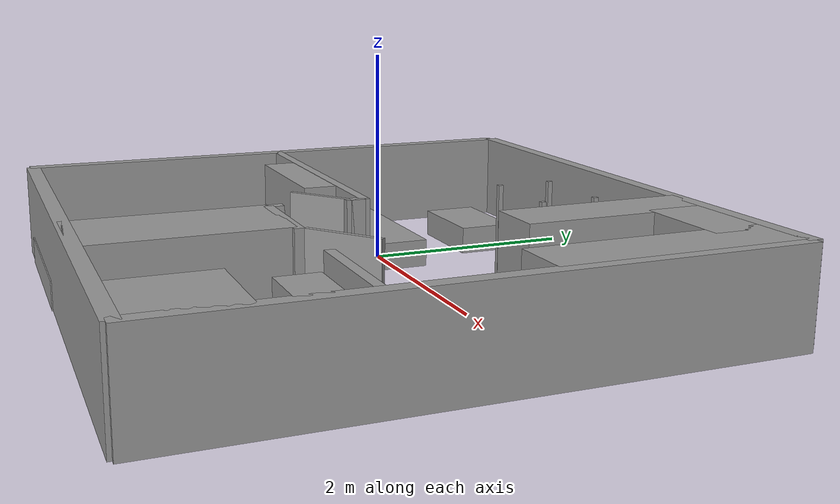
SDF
<?xml version='1.0'?>
<sdf version='1.7'>
  <model name='Apartment'>
    <link name='link_0'>
      <inertial>
        <mass>1</mass>
        <inertia>
          <ixx>0.166667</ixx>
          <ixy>0</ixy>
          <ixz>0</ixz>
          <iyy>0.166667</iyy>
          <iyz>0</iyz>
          <izz>0.166667</izz>
        </inertia>
        <pose>0 0 0 0 -0 0</pose>
      </inertial>
      <pose>-3.2479 -0.052565 0.051852 0 -0 0</pose>
      <gravity>1</gravity>
      <self_collide>0</self_collide>
      <kinematic>0</kinematic>
      <enable_wind>0</enable_wind>
      <visual name='visual'>
        <pose>0 0 0 0 -0 0</pose>
        <geometry>
          <box>
            <size>0.15 6 1</size>
          </box>
        </geometry>
        <material>
          <lighting>1</lighting>
          <script>
            <uri>file://media/materials/scripts/gazebo.material</uri>
            <name>Gazebo/Grey</name>
          </script>
          <shader type='pixel'>
            <normal_map>__default__</normal_map>
          </shader>
          <ambient>0.3 0.3 0.3 1</ambient>
          <diffuse>0.7 0.7 0.7 1</diffuse>
          <specular>0.01 0.01 0.01 1</specular>
          <emissive>0 0 0 1</emissive>
        </material>
        <transparency>0</transparency>
        <cast_shadows>1</cast_shadows>
      </visual>
      <collision name='collision'>
        <laser_retro>0</laser_retro>
        <max_contacts>10</max_contacts>
        <pose>0 0 0 0 -0 0</pose>
        <geometry>
          <box>
            <size>0.15 6 1</size>
          </box>
        </geometry>
        <surface>
          <friction>
            <ode>
              <mu>1</mu>
              <mu2>1</mu2>
              <fdir1>0 0 0</fdir1>
              <slip1>0</slip1>
              <slip2>0</slip2>
            </ode>
            <torsional>
              <coefficient>1</coefficient>
              <patch_radius>0</patch_radius>
              <surface_radius>0</surface_radius>
              <use_patch_radius>1</use_patch_radius>
              <ode>
                <slip>0</slip>
              </ode>
            </torsional>
          </friction>
          <bounce>
            <restitution_coefficient>0</restitution_coefficient>
            <threshold>1e+06</threshold>
          </bounce>
          <contact>
            <collide_without_contact>0</collide_without_contact>
            <collide_without_contact_bitmask>1</collide_without_contact_bitmask>
            <collide_bitmask>1</collide_bitmask>
            <ode>
              <soft_cfm>0</soft_cfm>
              <soft_erp>0.2</soft_erp>
              <kp>1e+13</kp>
              <kd>1</kd>
              <max_vel>0.01</max_vel>
              <min_depth>0</min_depth>
            </ode>
            <bullet>
              <split_impulse>1</split_impulse>
              <split_impulse_penetration_threshold>-0.01</split_impulse_penetration_threshold>
              <soft_cfm>0</soft_cfm>
              <soft_erp>0.2</soft_erp>
              <kp>1e+13</kp>
              <kd>1</kd>
            </bullet>
          </contact>
        </surface>
      </collision>
    </link>
    <link name='link_0_clone'>
      <inertial>
        <mass>1</mass>
        <inertia>
          <ixx>0.166667</ixx>
          <ixy>0</ixy>
          <ixz>0</ixz>
          <iyy>0.166667</iyy>
          <iyz>0</iyz>
          <izz>0.166667</izz>
        </inertia>
        <pose>0 0 0 0 -0 0</pose>
      </inertial>
      <pose>2.7521 -0.052565 0.051852 0 -0 0</pose>
      <gravity>1</gravity>
      <self_collide>0</self_collide>
      <kinematic>0</kinematic>
      <enable_wind>0</enable_wind>
      <visual name='visual'>
        <pose>0 0 0 0 -0 0</pose>
        <geometry>
          <box>
            <size>0.15 6 1</size>
          </box>
        </geometry>
        <material>
          <lighting>1</lighting>
          <script>
            <uri>file://media/materials/scripts/gazebo.material</uri>
            <name>Gazebo/Grey</name>
          </script>
          <shader type='pixel'>
            <normal_map>__default__</normal_map>
          </shader>
          <ambient>0.3 0.3 0.3 1</ambient>
          <diffuse>0.7 0.7 0.7 1</diffuse>
          <specular>0.01 0.01 0.01 1</specular>
          <emissive>0 0 0 1</emissive>
        </material>
        <transparency>0</transparency>
        <cast_shadows>1</cast_shadows>
      </visual>
      <collision name='collision'>
        <laser_retro>0</laser_retro>
        <max_contacts>10</max_contacts>
        <pose>0 0 0 0 -0 0</pose>
        <geometry>
          <box>
            <size>0.15 6 1</size>
          </box>
        </geometry>
        <surface>
          <friction>
            <ode>
              <mu>1</mu>
              <mu2>1</mu2>
              <fdir1>0 0 0</fdir1>
              <slip1>0</slip1>
              <slip2>0</slip2>
            </ode>
            <torsional>
              <coefficient>1</coefficient>
              <patch_radius>0</patch_radius>
              <surface_radius>0</surface_radius>
              <use_patch_radius>1</use_patch_radius>
              <ode>
                <slip>0</slip>
              </ode>
            </torsional>
          </friction>
          <bounce>
            <restitution_coefficient>0</restitution_coefficient>
            <threshold>1e+06</threshold>
          </bounce>
          <contact>
            <collide_without_contact>0</collide_without_contact>
            <collide_without_contact_bitmask>1</collide_without_contact_bitmask>
            <collide_bitmask>1</collide_bitmask>
            <ode>
              <soft_cfm>0</soft_cfm>
              <soft_erp>0.2</soft_erp>
              <kp>1e+13</kp>
              <kd>1</kd>
              <max_vel>0.01</max_vel>
              <min_depth>0</min_depth>
            </ode>
            <bullet>
              <split_impulse>1</split_impulse>
              <split_impulse_penetration_threshold>-0.01</split_impulse_penetration_threshold>
              <soft_cfm>0</soft_cfm>
              <soft_erp>0.2</soft_erp>
              <kp>1e+13</kp>
              <kd>1</kd>
            </bullet>
          </contact>
        </surface>
      </collision>
    </link>
    <link name='link_0_clone_clone'>
      <inertial>
        <mass>1</mass>
        <inertia>
          <ixx>0.166667</ixx>
          <ixy>0</ixy>
          <ixz>0</ixz>
          <iyy>0.166667</iyy>
          <iyz>0</iyz>
          <izz>0.166667</izz>
        </inertia>
        <pose>0 0 0 0 -0 0</pose>
      </inertial>
      <pose>-0.222232 -3.01597 0.051852 0 -0 0</pose>
      <gravity>1</gravity>
      <self_collide>0</self_collide>
      <kinematic>0</kinematic>
      <enable_wind>0</enable_wind>
      <visual name='visual'>
        <pose>0 0 0 0 -0 0</pose>
        <geometry>
          <box>
            <size>6 0.15 1</size>
          </box>
        </geometry>
        <material>
          <lighting>1</lighting>
          <script>
            <uri>file://media/materials/scripts/gazebo.material</uri>
            <name>Gazebo/Grey</name>
          </script>
          <shader type='pixel'>
            <normal_map>__default__</normal_map>
          </shader>
          <ambient>0.3 0.3 0.3 1</ambient>
          <diffuse>0.7 0.7 0.7 1</diffuse>
          <specular>0.01 0.01 0.01 1</specular>
          <emissive>0 0 0 1</emissive>
        </material>
        <transparency>0</transparency>
        <cast_shadows>1</cast_shadows>
      </visual>
      <collision name='collision'>
        <laser_retro>0</laser_retro>
        <max_contacts>10</max_contacts>
        <pose>0 0 0 0 -0 0</pose>
        <geometry>
          <box>
            <size>6 0.15 1</size>
          </box>
        </geometry>
        <surface>
          <friction>
            <ode>
              <mu>1</mu>
              <mu2>1</mu2>
              <fdir1>0 0 0</fdir1>
              <slip1>0</slip1>
              <slip2>0</slip2>
            </ode>
            <torsional>
              <coefficient>1</coefficient>
              <patch_radius>0</patch_radius>
              <surface_radius>0</surface_radius>
              <use_patch_radius>1</use_patch_radius>
              <ode>
                <slip>0</slip>
              </ode>
            </torsional>
          </friction>
          <bounce>
            <restitution_coefficient>0</restitution_coefficient>
            <threshold>1e+06</threshold>
          </bounce>
          <contact>
            <collide_without_contact>0</collide_without_contact>
            <collide_without_contact_bitmask>1</collide_without_contact_bitmask>
            <collide_bitmask>1</collide_bitmask>
            <ode>
              <soft_cfm>0</soft_cfm>
              <soft_erp>0.2</soft_erp>
              <kp>1e+13</kp>
              <kd>1</kd>
              <max_vel>0.01</max_vel>
              <min_depth>0</min_depth>
            </ode>
            <bullet>
              <split_impulse>1</split_impulse>
              <split_impulse_penetration_threshold>-0.01</split_impulse_penetration_threshold>
              <soft_cfm>0</soft_cfm>
              <soft_erp>0.2</soft_erp>
              <kp>1e+13</kp>
              <kd>1</kd>
            </bullet>
          </contact>
        </surface>
      </collision>
    </link>
    <link name='link_0_clone_clone_clone'>
      <inertial>
        <mass>1</mass>
        <inertia>
          <ixx>0.166667</ixx>
          <ixy>0</ixy>
          <ixz>0</ixz>
          <iyy>0.166667</iyy>
          <iyz>0</iyz>
          <izz>0.166667</izz>
        </inertia>
        <pose>0 0 0 0 -0 0</pose>
      </inertial>
      <pose>-0.247898 2.94744 0.051852 0 -0 0</pose>
      <gravity>1</gravity>
      <self_collide>0</self_collide>
      <kinematic>0</kinematic>
      <enable_wind>0</enable_wind>
      <visual name='visual'>
        <pose>0 0 0 0 -0 0</pose>
        <geometry>
          <box>
            <size>6 0.15 1</size>
          </box>
        </geometry>
        <material>
          <lighting>1</lighting>
          <script>
            <uri>file://media/materials/scripts/gazebo.material</uri>
            <name>Gazebo/Grey</name>
          </script>
          <shader type='pixel'>
            <normal_map>__default__</normal_map>
          </shader>
          <ambient>0.3 0.3 0.3 1</ambient>
          <diffuse>0.7 0.7 0.7 1</diffuse>
          <specular>0.01 0.01 0.01 1</specular>
          <emissive>0 0 0 1</emissive>
        </material>
        <transparency>0</transparency>
        <cast_shadows>1</cast_shadows>
      </visual>
      <collision name='collision'>
        <laser_retro>0</laser_retro>
        <max_contacts>10</max_contacts>
        <pose>0 0 0 0 -0 0</pose>
        <geometry>
          <box>
            <size>6 0.15 1</size>
          </box>
        </geometry>
        <surface>
          <friction>
            <ode>
              <mu>1</mu>
              <mu2>1</mu2>
              <fdir1>0 0 0</fdir1>
              <slip1>0</slip1>
              <slip2>0</slip2>
            </ode>
            <torsional>
              <coefficient>1</coefficient>
              <patch_radius>0</patch_radius>
              <surface_radius>0</surface_radius>
              <use_patch_radius>1</use_patch_radius>
              <ode>
                <slip>0</slip>
              </ode>
            </torsional>
          </friction>
          <bounce>
            <restitution_coefficient>0</restitution_coefficient>
            <threshold>1e+06</threshold>
          </bounce>
          <contact>
            <collide_without_contact>0</collide_without_contact>
            <collide_without_contact_bitmask>1</collide_without_contact_bitmask>
            <collide_bitmask>1</collide_bitmask>
            <ode>
              <soft_cfm>0</soft_cfm>
              <soft_erp>0.2</soft_erp>
              <kp>1e+13</kp>
              <kd>1</kd>
              <max_vel>0.01</max_vel>
              <min_depth>0</min_depth>
            </ode>
            <bullet>
              <split_impulse>1</split_impulse>
              <split_impulse_penetration_threshold>-0.01</split_impulse_penetration_threshold>
              <soft_cfm>0</soft_cfm>
              <soft_erp>0.2</soft_erp>
              <kp>1e+13</kp>
              <kd>1</kd>
            </bullet>
          </contact>
        </surface>
      </collision>
    </link>
    <link name='link_0_clone_clone_clone_clone'>
      <inertial>
        <mass>1</mass>
        <inertia>
          <ixx>0.166667</ixx>
          <ixy>0</ixy>
          <ixz>0</ixz>
          <iyy>0.166667</iyy>
          <iyz>0</iyz>
          <izz>0.166667</izz>
        </inertia>
        <pose>0 0 0 0 -0 0</pose>
      </inertial>
      <pose>-1.7479 -0.052565 0.051852 0 -0 0</pose>
      <gravity>1</gravity>
      <self_collide>0</self_collide>
      <kinematic>0</kinematic>
      <enable_wind>0</enable_wind>
      <visual name='visual'>
        <pose>0 0 0 0 -0 0</pose>
        <geometry>
          <box>
            <size>3 0.1 1</size>
          </box>
        </geometry>
        <material>
          <lighting>1</lighting>
          <script>
            <uri>file://media/materials/scripts/gazebo.material</uri>
            <name>Gazebo/Grey</name>
          </script>
          <shader type='pixel'>
            <normal_map>__default__</normal_map>
          </shader>
          <ambient>0.3 0.3 0.3 1</ambient>
          <diffuse>0.7 0.7 0.7 1</diffuse>
          <specular>0.01 0.01 0.01 1</specular>
          <emissive>0 0 0 1</emissive>
        </material>
        <transparency>0</transparency>
        <cast_shadows>1</cast_shadows>
      </visual>
      <collision name='collision'>
        <laser_retro>0</laser_retro>
        <max_contacts>10</max_contacts>
        <pose>0 0 0 0 -0 0</pose>
        <geometry>
          <box>
            <size>3 0.1 1</size>
          </box>
        </geometry>
        <surface>
          <friction>
            <ode>
              <mu>1</mu>
              <mu2>1</mu2>
              <fdir1>0 0 0</fdir1>
              <slip1>0</slip1>
              <slip2>0</slip2>
            </ode>
            <torsional>
              <coefficient>1</coefficient>
              <patch_radius>0</patch_radius>
              <surface_radius>0</surface_radius>
              <use_patch_radius>1</use_patch_radius>
              <ode>
                <slip>0</slip>
              </ode>
            </torsional>
          </friction>
          <bounce>
            <restitution_coefficient>0</restitution_coefficient>
            <threshold>1e+06</threshold>
          </bounce>
          <contact>
            <collide_without_contact>0</collide_without_contact>
            <collide_without_contact_bitmask>1</collide_without_contact_bitmask>
            <collide_bitmask>1</collide_bitmask>
            <ode>
              <soft_cfm>0</soft_cfm>
              <soft_erp>0.2</soft_erp>
              <kp>1e+13</kp>
              <kd>1</kd>
              <max_vel>0.01</max_vel>
              <min_depth>0</min_depth>
            </ode>
            <bullet>
              <split_impulse>1</split_impulse>
              <split_impulse_penetration_threshold>-0.01</split_impulse_penetration_threshold>
              <soft_cfm>0</soft_cfm>
              <soft_erp>0.2</soft_erp>
              <kp>1e+13</kp>
              <kd>1</kd>
            </bullet>
          </contact>
        </surface>
      </collision>
    </link>
    <link name='link_0_clone_clone_clone_clone_clone'>
      <inertial>
        <mass>1</mass>
        <inertia>
          <ixx>0.166667</ixx>
          <ixy>0</ixy>
          <ixz>0</ixz>
          <iyy>0.166667</iyy>
          <iyz>0</iyz>
          <izz>0.166667</izz>
        </inertia>
        <pose>0 0 0 0 -0 0</pose>
      </inertial>
      <pose>2.1521 -1.05256 0.051852 0 -0 0</pose>
      <gravity>1</gravity>
      <self_collide>0</self_collide>
      <kinematic>0</kinematic>
      <enable_wind>0</enable_wind>
      <visual name='visual'>
        <pose>0 0 0 0 -0 0</pose>
        <geometry>
          <box>
            <size>1.2 0.1 1</size>
          </box>
        </geometry>
        <material>
          <lighting>1</lighting>
          <script>
            <uri>file://media/materials/scripts/gazebo.material</uri>
            <name>Gazebo/Grey</name>
          </script>
          <shader type='pixel'>
            <normal_map>__default__</normal_map>
          </shader>
          <ambient>0.3 0.3 0.3 1</ambient>
          <diffuse>0.7 0.7 0.7 1</diffuse>
          <specular>0.01 0.01 0.01 1</specular>
          <emissive>0 0 0 1</emissive>
        </material>
        <transparency>0</transparency>
        <cast_shadows>1</cast_shadows>
      </visual>
      <collision name='collision'>
        <laser_retro>0</laser_retro>
        <max_contacts>10</max_contacts>
        <pose>0 0 0 0 -0 0</pose>
        <geometry>
          <box>
            <size>1.2 0.1 1</size>
          </box>
        </geometry>
        <surface>
          <friction>
            <ode>
              <mu>1</mu>
              <mu2>1</mu2>
              <fdir1>0 0 0</fdir1>
              <slip1>0</slip1>
              <slip2>0</slip2>
            </ode>
            <torsional>
              <coefficient>1</coefficient>
              <patch_radius>0</patch_radius>
              <surface_radius>0</surface_radius>
              <use_patch_radius>1</use_patch_radius>
              <ode>
                <slip>0</slip>
              </ode>
            </torsional>
          </friction>
          <bounce>
            <restitution_coefficient>0</restitution_coefficient>
            <threshold>1e+06</threshold>
          </bounce>
          <contact>
            <collide_without_contact>0</collide_without_contact>
            <collide_without_contact_bitmask>1</collide_without_contact_bitmask>
            <collide_bitmask>1</collide_bitmask>
            <ode>
              <soft_cfm>0</soft_cfm>
              <soft_erp>0.2</soft_erp>
              <kp>1e+13</kp>
              <kd>1</kd>
              <max_vel>0.01</max_vel>
              <min_depth>0</min_depth>
            </ode>
            <bullet>
              <split_impulse>1</split_impulse>
              <split_impulse_penetration_threshold>-0.01</split_impulse_penetration_threshold>
              <soft_cfm>0</soft_cfm>
              <soft_erp>0.2</soft_erp>
              <kp>1e+13</kp>
              <kd>1</kd>
            </bullet>
          </contact>
        </surface>
      </collision>
    </link>
    <link name='link_0_clone_clone_clone_clone_clone_clone'>
      <inertial>
        <mass>1</mass>
        <inertia>
          <ixx>0.166667</ixx>
          <ixy>0</ixy>
          <ixz>0</ixz>
          <iyy>0.166667</iyy>
          <iyz>0</iyz>
          <izz>0.166667</izz>
        </inertia>
        <pose>0 0 0 0 -0 0</pose>
      </inertial>
      <pose>0.252102 -1.05256 0.051852 0 -0 0</pose>
      <gravity>1</gravity>
      <self_collide>0</self_collide>
      <kinematic>0</kinematic>
      <enable_wind>0</enable_wind>
      <visual name='visual'>
        <pose>0 0 0 0 -0 0</pose>
        <geometry>
          <box>
            <size>1 0.1 1</size>
          </box>
        </geometry>
        <material>
          <lighting>1</lighting>
          <script>
            <uri>file://media/materials/scripts/gazebo.material</uri>
            <name>Gazebo/Grey</name>
          </script>
          <shader type='pixel'>
            <normal_map>__default__</normal_map>
          </shader>
          <ambient>0.3 0.3 0.3 1</ambient>
          <diffuse>0.7 0.7 0.7 1</diffuse>
          <specular>0.01 0.01 0.01 1</specular>
          <emissive>0 0 0 1</emissive>
        </material>
        <transparency>0</transparency>
        <cast_shadows>1</cast_shadows>
      </visual>
      <collision name='collision'>
        <laser_retro>0</laser_retro>
        <max_contacts>10</max_contacts>
        <pose>0 0 0 0 -0 0</pose>
        <geometry>
          <box>
            <size>1 0.1 1</size>
          </box>
        </geometry>
        <surface>
          <friction>
            <ode>
              <mu>1</mu>
              <mu2>1</mu2>
              <fdir1>0 0 0</fdir1>
              <slip1>0</slip1>
              <slip2>0</slip2>
            </ode>
            <torsional>
              <coefficient>1</coefficient>
              <patch_radius>0</patch_radius>
              <surface_radius>0</surface_radius>
              <use_patch_radius>1</use_patch_radius>
              <ode>
                <slip>0</slip>
              </ode>
            </torsional>
          </friction>
          <bounce>
            <restitution_coefficient>0</restitution_coefficient>
            <threshold>1e+06</threshold>
          </bounce>
          <contact>
            <collide_without_contact>0</collide_without_contact>
            <collide_without_contact_bitmask>1</collide_without_contact_bitmask>
            <collide_bitmask>1</collide_bitmask>
            <ode>
              <soft_cfm>0</soft_cfm>
              <soft_erp>0.2</soft_erp>
              <kp>1e+13</kp>
              <kd>1</kd>
              <max_vel>0.01</max_vel>
              <min_depth>0</min_depth>
            </ode>
            <bullet>
              <split_impulse>1</split_impulse>
              <split_impulse_penetration_threshold>-0.01</split_impulse_penetration_threshold>
              <soft_cfm>0</soft_cfm>
              <soft_erp>0.2</soft_erp>
              <kp>1e+13</kp>
              <kd>1</kd>
            </bullet>
          </contact>
        </surface>
      </collision>
    </link>
    <link name='link_0_clone_clone_clone_clone_clone_clone_clone'>
      <inertial>
        <mass>9.80531</mass>
        <inertia>
          <ixx>4.08555</ixx>
          <ixy>0</ixy>
          <ixz>0</ixz>
          <iyy>1.60274</iyy>
          <iyz>0</iyz>
          <izz>4.05407</izz>
        </inertia>
        <pose>0 0 0 0 -0 0</pose>
      </inertial>
      <pose>0.197236 -2.05256 0.051852 0 -0 0</pose>
      <gravity>1</gravity>
      <self_collide>0</self_collide>
      <kinematic>0</kinematic>
      <enable_wind>0</enable_wind>
      <visual name='visual'>
        <pose>0 0 0 0 -0 0</pose>
        <geometry>
          <box>
            <size>1 2 1</size>
          </box>
        </geometry>
        <material>
          <lighting>1</lighting>
          <script>
            <uri>file://media/materials/scripts/gazebo.material</uri>
            <name>Gazebo/Grey</name>
          </script>
          <shader type='pixel'>
            <normal_map>__default__</normal_map>
          </shader>
          <ambient>0.3 0.3 0.3 1</ambient>
          <diffuse>0.7 0.7 0.7 1</diffuse>
          <specular>0.01 0.01 0.01 1</specular>
          <emissive>0 0 0 1</emissive>
        </material>
        <transparency>0</transparency>
        <cast_shadows>1</cast_shadows>
      </visual>
      <collision name='collision'>
        <laser_retro>0</laser_retro>
        <max_contacts>10</max_contacts>
        <pose>0 0 0 0 -0 0</pose>
        <geometry>
          <box>
            <size>1 2 1</size>
          </box>
        </geometry>
        <surface>
          <friction>
            <ode>
              <mu>1</mu>
              <mu2>1</mu2>
              <fdir1>0 0 0</fdir1>
              <slip1>0</slip1>
              <slip2>0</slip2>
            </ode>
            <torsional>
              <coefficient>1</coefficient>
              <patch_radius>0</patch_radius>
              <surface_radius>0</surface_radius>
              <use_patch_radius>1</use_patch_radius>
              <ode>
                <slip>0</slip>
              </ode>
            </torsional>
          </friction>
          <bounce>
            <restitution_coefficient>0</restitution_coefficient>
            <threshold>1e+06</threshold>
          </bounce>
          <contact>
            <collide_without_contact>0</collide_without_contact>
            <collide_without_contact_bitmask>1</collide_without_contact_bitmask>
            <collide_bitmask>1</collide_bitmask>
            <ode>
              <soft_cfm>0</soft_cfm>
              <soft_erp>0.2</soft_erp>
              <kp>1e+13</kp>
              <kd>1</kd>
              <max_vel>0.01</max_vel>
              <min_depth>0</min_depth>
            </ode>
            <bullet>
              <split_impulse>1</split_impulse>
              <split_impulse_penetration_threshold>-0.01</split_impulse_penetration_threshold>
              <soft_cfm>0</soft_cfm>
              <soft_erp>0.2</soft_erp>
              <kp>1e+13</kp>
              <kd>1</kd>
            </bullet>
          </contact>
        </surface>
      </collision>
    </link>
    <link name='link_0_clone_clone_clone_clone_clone_clone_clone_0'>
      <inertial>
        <mass>1</mass>
        <inertia>
          <ixx>0.166667</ixx>
          <ixy>0</ixy>
          <ixz>0</ixz>
          <iyy>0.166667</iyy>
          <iyz>0</iyz>
          <izz>0.166667</izz>
        </inertia>
        <pose>0 0 0 0 -0 0</pose>
      </inertial>
      <pose>-0.247898 -1.05256 0.051852 0 -0 0</pose>
      <gravity>1</gravity>
      <self_collide>0</self_collide>
      <kinematic>0</kinematic>
      <enable_wind>0</enable_wind>
      <visual name='visual'>
        <pose>0 0 0 0 -0 0</pose>
        <geometry>
          <box>
            <size>0.1 0.3 1</size>
          </box>
        </geometry>
        <material>
          <lighting>1</lighting>
          <script>
            <uri>file://media/materials/scripts/gazebo.material</uri>
            <name>Gazebo/Grey</name>
          </script>
          <shader type='pixel'>
            <normal_map>__default__</normal_map>
          </shader>
          <ambient>0.3 0.3 0.3 1</ambient>
          <diffuse>0.7 0.7 0.7 1</diffuse>
          <specular>0.01 0.01 0.01 1</specular>
          <emissive>0 0 0 1</emissive>
        </material>
        <transparency>0</transparency>
        <cast_shadows>1</cast_shadows>
      </visual>
      <collision name='collision'>
        <laser_retro>0</laser_retro>
        <max_contacts>10</max_contacts>
        <pose>0 0 0 0 -0 0</pose>
        <geometry>
          <box>
            <size>0.1 0.3 1</size>
          </box>
        </geometry>
        <surface>
          <friction>
            <ode>
              <mu>1</mu>
              <mu2>1</mu2>
              <fdir1>0 0 0</fdir1>
              <slip1>0</slip1>
              <slip2>0</slip2>
            </ode>
            <torsional>
              <coefficient>1</coefficient>
              <patch_radius>0</patch_radius>
              <surface_radius>0</surface_radius>
              <use_patch_radius>1</use_patch_radius>
              <ode>
                <slip>0</slip>
              </ode>
            </torsional>
          </friction>
          <bounce>
            <restitution_coefficient>0</restitution_coefficient>
            <threshold>1e+06</threshold>
          </bounce>
          <contact>
            <collide_without_contact>0</collide_without_contact>
            <collide_without_contact_bitmask>1</collide_without_contact_bitmask>
            <collide_bitmask>1</collide_bitmask>
            <ode>
              <soft_cfm>0</soft_cfm>
              <soft_erp>0.2</soft_erp>
              <kp>1e+13</kp>
              <kd>1</kd>
              <max_vel>0.01</max_vel>
              <min_depth>0</min_depth>
            </ode>
            <bullet>
              <split_impulse>1</split_impulse>
              <split_impulse_penetration_threshold>-0.01</split_impulse_penetration_threshold>
              <soft_cfm>0</soft_cfm>
              <soft_erp>0.2</soft_erp>
              <kp>1e+13</kp>
              <kd>1</kd>
            </bullet>
          </contact>
        </surface>
      </collision>
    </link>
    <link name='link_0_clone_clone_clone_clone_clone_clone_clone_0_clone'>
      <inertial>
        <mass>1</mass>
        <inertia>
          <ixx>0.166667</ixx>
          <ixy>0</ixy>
          <ixz>0</ixz>
          <iyy>0.166667</iyy>
          <iyz>0</iyz>
          <izz>0.166667</izz>
        </inertia>
        <pose>0 0 0 0 -0 0</pose>
      </inertial>
      <pose>-0.247898 -0.152565 0.051852 0 -0 0</pose>
      <gravity>1</gravity>
      <self_collide>0</self_collide>
      <kinematic>0</kinematic>
      <enable_wind>0</enable_wind>
      <visual name='visual'>
        <pose>0 0 0 0 -0 0</pose>
        <geometry>
          <box>
            <size>0.1 0.2 1</size>
          </box>
        </geometry>
        <material>
          <lighting>1</lighting>
          <script>
            <uri>file://media/materials/scripts/gazebo.material</uri>
            <name>Gazebo/Grey</name>
          </script>
          <shader type='pixel'>
            <normal_map>__default__</normal_map>
          </shader>
          <ambient>0.3 0.3 0.3 1</ambient>
          <diffuse>0.7 0.7 0.7 1</diffuse>
          <specular>0.01 0.01 0.01 1</specular>
          <emissive>0 0 0 1</emissive>
        </material>
        <transparency>0</transparency>
        <cast_shadows>1</cast_shadows>
      </visual>
      <collision name='collision'>
        <laser_retro>0</laser_retro>
        <max_contacts>10</max_contacts>
        <pose>0 0 0 0 -0 0</pose>
        <geometry>
          <box>
            <size>0.1 0.2 1</size>
          </box>
        </geometry>
        <surface>
          <friction>
            <ode>
              <mu>1</mu>
              <mu2>1</mu2>
              <fdir1>0 0 0</fdir1>
              <slip1>0</slip1>
              <slip2>0</slip2>
            </ode>
            <torsional>
              <coefficient>1</coefficient>
              <patch_radius>0</patch_radius>
              <surface_radius>0</surface_radius>
              <use_patch_radius>1</use_patch_radius>
              <ode>
                <slip>0</slip>
              </ode>
            </torsional>
          </friction>
          <bounce>
            <restitution_coefficient>0</restitution_coefficient>
            <threshold>1e+06</threshold>
          </bounce>
          <contact>
            <collide_without_contact>0</collide_without_contact>
            <collide_without_contact_bitmask>1</collide_without_contact_bitmask>
            <collide_bitmask>1</collide_bitmask>
            <ode>
              <soft_cfm>0</soft_cfm>
              <soft_erp>0.2</soft_erp>
              <kp>1e+13</kp>
              <kd>1</kd>
              <max_vel>0.01</max_vel>
              <min_depth>0</min_depth>
            </ode>
            <bullet>
              <split_impulse>1</split_impulse>
              <split_impulse_penetration_threshold>-0.01</split_impulse_penetration_threshold>
              <soft_cfm>0</soft_cfm>
              <soft_erp>0.2</soft_erp>
              <kp>1e+13</kp>
              <kd>1</kd>
            </bullet>
          </contact>
        </surface>
      </collision>
    </link>
    <link name='link_0_clone_clone_clone_clone_clone_clone_clone_0_clone_0'>
      <inertial>
        <mass>1</mass>
        <inertia>
          <ixx>0.166667</ixx>
          <ixy>0</ixy>
          <ixz>0</ixz>
          <iyy>0.166667</iyy>
          <iyz>0</iyz>
          <izz>0.166667</izz>
        </inertia>
        <pose>0 0 0 0 -0 0</pose>
      </inertial>
      <pose>-0.247898 -0.102565 0.051852 0 -0 0</pose>
      <gravity>1</gravity>
      <self_collide>0</self_collide>
      <kinematic>0</kinematic>
      <enable_wind>0</enable_wind>
      <visual name='visual'>
        <pose>0 0 0 0 -0 0</pose>
        <geometry>
          <box>
            <size>0.1 0.2 1</size>
          </box>
        </geometry>
        <material>
          <lighting>1</lighting>
          <script>
            <uri>file://media/materials/scripts/gazebo.material</uri>
            <name>Gazebo/Grey</name>
          </script>
          <shader type='pixel'>
            <normal_map>__default__</normal_map>
          </shader>
          <ambient>0.3 0.3 0.3 1</ambient>
          <diffuse>0.7 0.7 0.7 1</diffuse>
          <specular>0.01 0.01 0.01 1</specular>
          <emissive>0 0 0 1</emissive>
        </material>
        <transparency>0</transparency>
        <cast_shadows>1</cast_shadows>
      </visual>
      <collision name='collision'>
        <laser_retro>0</laser_retro>
        <max_contacts>10</max_contacts>
        <pose>0 0 0 0 -0 0</pose>
        <geometry>
          <box>
            <size>0.1 0.2 1</size>
          </box>
        </geometry>
        <surface>
          <friction>
            <ode>
              <mu>1</mu>
              <mu2>1</mu2>
              <fdir1>0 0 0</fdir1>
              <slip1>0</slip1>
              <slip2>0</slip2>
            </ode>
            <torsional>
              <coefficient>1</coefficient>
              <patch_radius>0</patch_radius>
              <surface_radius>0</surface_radius>
              <use_patch_radius>1</use_patch_radius>
              <ode>
                <slip>0</slip>
              </ode>
            </torsional>
          </friction>
          <bounce>
            <restitution_coefficient>0</restitution_coefficient>
            <threshold>1e+06</threshold>
          </bounce>
          <contact>
            <collide_without_contact>0</collide_without_contact>
            <collide_without_contact_bitmask>1</collide_without_contact_bitmask>
            <collide_bitmask>1</collide_bitmask>
            <ode>
              <soft_cfm>0</soft_cfm>
              <soft_erp>0.2</soft_erp>
              <kp>1e+13</kp>
              <kd>1</kd>
              <max_vel>0.01</max_vel>
              <min_depth>0</min_depth>
            </ode>
            <bullet>
              <split_impulse>1</split_impulse>
              <split_impulse_penetration_threshold>-0.01</split_impulse_penetration_threshold>
              <soft_cfm>0</soft_cfm>
              <soft_erp>0.2</soft_erp>
              <kp>1e+13</kp>
              <kd>1</kd>
            </bullet>
          </contact>
        </surface>
      </collision>
    </link>
    <link name='link_0_clone_clone_clone_clone_clone_clone_clone_0_clone_1'>
      <inertial>
        <mass>1</mass>
        <inertia>
          <ixx>0.166667</ixx>
          <ixy>0</ixy>
          <ixz>0</ixz>
          <iyy>0.166667</iyy>
          <iyz>0</iyz>
          <izz>0.166667</izz>
        </inertia>
        <pose>0 0 0 0 -0 0</pose>
      </inertial>
      <pose>-0.540177 -0.421865 0.051852 0 0 -0.9</pose>
      <gravity>1</gravity>
      <self_collide>0</self_collide>
      <kinematic>0</kinematic>
      <enable_wind>0</enable_wind>
      <visual name='visual'>
        <pose>0 0 0 0 -0 0</pose>
        <geometry>
          <box>
            <size>0.05 0.7 1</size>
          </box>
        </geometry>
        <material>
          <lighting>1</lighting>
          <script>
            <uri>file://media/materials/scripts/gazebo.material</uri>
            <name>Gazebo/Grey</name>
          </script>
          <shader type='pixel'>
            <normal_map>__default__</normal_map>
          </shader>
          <ambient>0.3 0.3 0.3 1</ambient>
          <diffuse>0.7 0.7 0.7 1</diffuse>
          <specular>0.01 0.01 0.01 1</specular>
          <emissive>0 0 0 1</emissive>
        </material>
        <transparency>0</transparency>
        <cast_shadows>1</cast_shadows>
      </visual>
      <collision name='collision'>
        <laser_retro>0</laser_retro>
        <max_contacts>10</max_contacts>
        <pose>0 0 0 0 -0 0</pose>
        <geometry>
          <box>
            <size>0.05 0.7 1</size>
          </box>
        </geometry>
        <surface>
          <friction>
            <ode>
              <mu>1</mu>
              <mu2>1</mu2>
              <fdir1>0 0 0</fdir1>
              <slip1>0</slip1>
              <slip2>0</slip2>
            </ode>
            <torsional>
              <coefficient>1</coefficient>
              <patch_radius>0</patch_radius>
              <surface_radius>0</surface_radius>
              <use_patch_radius>1</use_patch_radius>
              <ode>
                <slip>0</slip>
              </ode>
            </torsional>
          </friction>
          <bounce>
            <restitution_coefficient>0</restitution_coefficient>
            <threshold>1e+06</threshold>
          </bounce>
          <contact>
            <collide_without_contact>0</collide_without_contact>
            <collide_without_contact_bitmask>1</collide_without_contact_bitmask>
            <collide_bitmask>1</collide_bitmask>
            <ode>
              <soft_cfm>0</soft_cfm>
              <soft_erp>0.2</soft_erp>
              <kp>1e+13</kp>
              <kd>1</kd>
              <max_vel>0.01</max_vel>
              <min_depth>0</min_depth>
            </ode>
            <bullet>
              <split_impulse>1</split_impulse>
              <split_impulse_penetration_threshold>-0.01</split_impulse_penetration_threshold>
              <soft_cfm>0</soft_cfm>
              <soft_erp>0.2</soft_erp>
              <kp>1e+13</kp>
              <kd>1</kd>
            </bullet>
          </contact>
        </surface>
      </collision>
    </link>
    <link name='link_0_clone_clone_clone_clone_clone_clone_clone_0_clone_1_clone_0'>
      <inertial>
        <mass>1</mass>
        <inertia>
          <ixx>0.166667</ixx>
          <ixy>0</ixy>
          <ixz>0</ixz>
          <iyy>0.166667</iyy>
          <iyz>0</iyz>
          <izz>0.166667</izz>
        </inertia>
        <pose>0 0 0 0 -0 0</pose>
      </inertial>
      <pose>1.05963 -0.743859 0.051852 0 0 -0.9</pose>
      <gravity>1</gravity>
      <self_collide>0</self_collide>
      <kinematic>0</kinematic>
      <enable_wind>0</enable_wind>
      <visual name='visual'>
        <pose>0 0 0 0 -0 0</pose>
        <geometry>
          <box>
            <size>0.05 0.8 1</size>
          </box>
        </geometry>
        <material>
          <lighting>1</lighting>
          <script>
            <uri>file://media/materials/scripts/gazebo.material</uri>
            <name>Gazebo/Grey</name>
          </script>
          <shader type='pixel'>
            <normal_map>__default__</normal_map>
          </shader>
          <ambient>0.3 0.3 0.3 1</ambient>
          <diffuse>0.7 0.7 0.7 1</diffuse>
          <specular>0.01 0.01 0.01 1</specular>
          <emissive>0 0 0 1</emissive>
        </material>
        <transparency>0</transparency>
        <cast_shadows>1</cast_shadows>
      </visual>
      <collision name='collision'>
        <laser_retro>0</laser_retro>
        <max_contacts>10</max_contacts>
        <pose>0 0 0 0 -0 0</pose>
        <geometry>
          <box>
            <size>0.05 0.8 1</size>
          </box>
        </geometry>
        <surface>
          <friction>
            <ode>
              <mu>1</mu>
              <mu2>1</mu2>
              <fdir1>0 0 0</fdir1>
              <slip1>0</slip1>
              <slip2>0</slip2>
            </ode>
            <torsional>
              <coefficient>1</coefficient>
              <patch_radius>0</patch_radius>
              <surface_radius>0</surface_radius>
              <use_patch_radius>1</use_patch_radius>
              <ode>
                <slip>0</slip>
              </ode>
            </torsional>
          </friction>
          <bounce>
            <restitution_coefficient>0</restitution_coefficient>
            <threshold>1e+06</threshold>
          </bounce>
          <contact>
            <collide_without_contact>0</collide_without_contact>
            <collide_without_contact_bitmask>1</collide_without_contact_bitmask>
            <collide_bitmask>1</collide_bitmask>
            <ode>
              <soft_cfm>0</soft_cfm>
              <soft_erp>0.2</soft_erp>
              <kp>1e+13</kp>
              <kd>1</kd>
              <max_vel>0.01</max_vel>
              <min_depth>0</min_depth>
            </ode>
            <bullet>
              <split_impulse>1</split_impulse>
              <split_impulse_penetration_threshold>-0.01</split_impulse_penetration_threshold>
              <soft_cfm>0</soft_cfm>
              <soft_erp>0.2</soft_erp>
              <kp>1e+13</kp>
              <kd>1</kd>
            </bullet>
          </contact>
        </surface>
      </collision>
    </link>
    <link name='link_1'>
      <inertial>
        <mass>1</mass>
        <inertia>
          <ixx>0.166667</ixx>
          <ixy>0</ixy>
          <ixz>0</ixz>
          <iyy>0.166667</iyy>
          <iyz>0</iyz>
          <izz>0.166667</izz>
        </inertia>
        <pose>0 0 0 0 -0 0</pose>
      </inertial>
      <pose>2.4021 1.69744 0.051852 0 -0 0</pose>
      <gravity>1</gravity>
      <self_collide>0</self_collide>
      <kinematic>0</kinematic>
      <enable_wind>0</enable_wind>
      <visual name='visual'>
        <pose>0 0 0 0 -0 0</pose>
        <geometry>
          <box>
            <size>0.6 2.5 1</size>
          </box>
        </geometry>
        <material>
          <lighting>1</lighting>
          <script>
            <uri>file://media/materials/scripts/gazebo.material</uri>
            <name>Gazebo/Grey</name>
          </script>
          <shader type='pixel'>
            <normal_map>__default__</normal_map>
          </shader>
          <ambient>0.3 0.3 0.3 1</ambient>
          <diffuse>0.7 0.7 0.7 1</diffuse>
          <specular>0.01 0.01 0.01 1</specular>
          <emissive>0 0 0 1</emissive>
        </material>
        <transparency>0</transparency>
        <cast_shadows>1</cast_shadows>
      </visual>
      <collision name='collision'>
        <laser_retro>0</laser_retro>
        <max_contacts>10</max_contacts>
        <pose>0 0 0 0 -0 0</pose>
        <geometry>
          <box>
            <size>0.6 2.5 1</size>
          </box>
        </geometry>
        <surface>
          <friction>
            <ode>
              <mu>1</mu>
              <mu2>1</mu2>
              <fdir1>0 0 0</fdir1>
              <slip1>0</slip1>
              <slip2>0</slip2>
            </ode>
            <torsional>
              <coefficient>1</coefficient>
              <patch_radius>0</patch_radius>
              <surface_radius>0</surface_radius>
              <use_patch_radius>1</use_patch_radius>
              <ode>
                <slip>0</slip>
              </ode>
            </torsional>
          </friction>
          <bounce>
            <restitution_coefficient>0</restitution_coefficient>
            <threshold>1e+06</threshold>
          </bounce>
          <contact>
            <collide_without_contact>0</collide_without_contact>
            <collide_without_contact_bitmask>1</collide_without_contact_bitmask>
            <collide_bitmask>1</collide_bitmask>
            <ode>
              <soft_cfm>0</soft_cfm>
              <soft_erp>0.2</soft_erp>
              <kp>1e+13</kp>
              <kd>1</kd>
              <max_vel>0.01</max_vel>
              <min_depth>0</min_depth>
            </ode>
            <bullet>
              <split_impulse>1</split_impulse>
              <split_impulse_penetration_threshold>-0.01</split_impulse_penetration_threshold>
              <soft_cfm>0</soft_cfm>
              <soft_erp>0.2</soft_erp>
              <kp>1e+13</kp>
              <kd>1</kd>
            </bullet>
          </contact>
        </surface>
      </collision>
    </link>
    <link name='link_1_clone'>
      <inertial>
        <mass>1</mass>
        <inertia>
          <ixx>0.166667</ixx>
          <ixy>0</ixy>
          <ixz>0</ixz>
          <iyy>0.166667</iyy>
          <iyz>0</iyz>
          <izz>0.166667</izz>
        </inertia>
        <pose>0 0 0 0 -0 0</pose>
      </inertial>
      <pose>1.0521 1.94744 0.051852 0 -0 0</pose>
      <gravity>1</gravity>
      <self_collide>0</self_collide>
      <kinematic>0</kinematic>
      <enable_wind>0</enable_wind>
      <visual name='visual'>
        <pose>0 0 0 0 -0 0</pose>
        <geometry>
          <box>
            <size>0.6 2 1</size>
          </box>
        </geometry>
        <material>
          <lighting>1</lighting>
          <script>
            <uri>file://media/materials/scripts/gazebo.material</uri>
            <name>Gazebo/Grey</name>
          </script>
          <shader type='pixel'>
            <normal_map>__default__</normal_map>
          </shader>
          <ambient>0.3 0.3 0.3 1</ambient>
          <diffuse>0.7 0.7 0.7 1</diffuse>
          <specular>0.01 0.01 0.01 1</specular>
          <emissive>0 0 0 1</emissive>
        </material>
        <transparency>0</transparency>
        <cast_shadows>1</cast_shadows>
      </visual>
      <collision name='collision'>
        <laser_retro>0</laser_retro>
        <max_contacts>10</max_contacts>
        <pose>0 0 0 0 -0 0</pose>
        <geometry>
          <box>
            <size>0.6 2 1</size>
          </box>
        </geometry>
        <surface>
          <friction>
            <ode>
              <mu>1</mu>
              <mu2>1</mu2>
              <fdir1>0 0 0</fdir1>
              <slip1>0</slip1>
              <slip2>0</slip2>
            </ode>
            <torsional>
              <coefficient>1</coefficient>
              <patch_radius>0</patch_radius>
              <surface_radius>0</surface_radius>
              <use_patch_radius>1</use_patch_radius>
              <ode>
                <slip>0</slip>
              </ode>
            </torsional>
          </friction>
          <bounce>
            <restitution_coefficient>0</restitution_coefficient>
            <threshold>1e+06</threshold>
          </bounce>
          <contact>
            <collide_without_contact>0</collide_without_contact>
            <collide_without_contact_bitmask>1</collide_without_contact_bitmask>
            <collide_bitmask>1</collide_bitmask>
            <ode>
              <soft_cfm>0</soft_cfm>
              <soft_erp>0.2</soft_erp>
              <kp>1e+13</kp>
              <kd>1</kd>
              <max_vel>0.01</max_vel>
              <min_depth>0</min_depth>
            </ode>
            <bullet>
              <split_impulse>1</split_impulse>
              <split_impulse_penetration_threshold>-0.01</split_impulse_penetration_threshold>
              <soft_cfm>0</soft_cfm>
              <soft_erp>0.2</soft_erp>
              <kp>1e+13</kp>
              <kd>1</kd>
            </bullet>
          </contact>
        </surface>
      </collision>
    </link>
    <link name='link_1_clone_clone'>
      <inertial>
        <mass>1</mass>
        <inertia>
          <ixx>0.166667</ixx>
          <ixy>0</ixy>
          <ixz>0</ixz>
          <iyy>0.166667</iyy>
          <iyz>0</iyz>
          <izz>0.166667</izz>
        </inertia>
        <pose>0 0 0 0 -0 0</pose>
      </inertial>
      <pose>1.7521 2.59743 0.051852 0 -0 0</pose>
      <gravity>1</gravity>
      <self_collide>0</self_collide>
      <kinematic>0</kinematic>
      <enable_wind>0</enable_wind>
      <visual name='visual'>
        <pose>0 0 0 0 -0 0</pose>
        <geometry>
          <box>
            <size>1 0.6 1</size>
          </box>
        </geometry>
        <material>
          <lighting>1</lighting>
          <script>
            <uri>file://media/materials/scripts/gazebo.material</uri>
            <name>Gazebo/Grey</name>
          </script>
          <shader type='pixel'>
            <normal_map>__default__</normal_map>
          </shader>
          <ambient>0.3 0.3 0.3 1</ambient>
          <diffuse>0.7 0.7 0.7 1</diffuse>
          <specular>0.01 0.01 0.01 1</specular>
          <emissive>0 0 0 1</emissive>
        </material>
        <transparency>0</transparency>
        <cast_shadows>1</cast_shadows>
      </visual>
      <collision name='collision'>
        <laser_retro>0</laser_retro>
        <max_contacts>10</max_contacts>
        <pose>0 0 0 0 -0 0</pose>
        <geometry>
          <box>
            <size>1 0.6 1</size>
          </box>
        </geometry>
        <surface>
          <friction>
            <ode>
              <mu>1</mu>
              <mu2>1</mu2>
              <fdir1>0 0 0</fdir1>
              <slip1>0</slip1>
              <slip2>0</slip2>
            </ode>
            <torsional>
              <coefficient>1</coefficient>
              <patch_radius>0</patch_radius>
              <surface_radius>0</surface_radius>
              <use_patch_radius>1</use_patch_radius>
              <ode>
                <slip>0</slip>
              </ode>
            </torsional>
          </friction>
          <bounce>
            <restitution_coefficient>0</restitution_coefficient>
            <threshold>1e+06</threshold>
          </bounce>
          <contact>
            <collide_without_contact>0</collide_without_contact>
            <collide_without_contact_bitmask>1</collide_without_contact_bitmask>
            <collide_bitmask>1</collide_bitmask>
            <ode>
              <soft_cfm>0</soft_cfm>
              <soft_erp>0.2</soft_erp>
              <kp>1e+13</kp>
              <kd>1</kd>
              <max_vel>0.01</max_vel>
              <min_depth>0</min_depth>
            </ode>
            <bullet>
              <split_impulse>1</split_impulse>
              <split_impulse_penetration_threshold>-0.01</split_impulse_penetration_threshold>
              <soft_cfm>0</soft_cfm>
              <soft_erp>0.2</soft_erp>
              <kp>1e+13</kp>
              <kd>1</kd>
            </bullet>
          </contact>
        </surface>
      </collision>
    </link>
    <link name='link_2'>
      <inertial>
        <mass>1</mass>
        <inertia>
          <ixx>0.166667</ixx>
          <ixy>0</ixy>
          <ixz>0</ixz>
          <iyy>0.166667</iyy>
          <iyz>0</iyz>
          <izz>0.166667</izz>
        </inertia>
        <pose>0 0 0 0 -0 0</pose>
      </inertial>
      <pose>2.3021 -2.50257 0.051852 0 -0 0</pose>
      <gravity>1</gravity>
      <self_collide>0</self_collide>
      <kinematic>0</kinematic>
      <enable_wind>0</enable_wind>
      <visual name='visual'>
        <pose>0 0 0 0 -0 0</pose>
        <geometry>
          <box>
            <size>1 1 1</size>
          </box>
        </geometry>
        <material>
          <lighting>1</lighting>
          <script>
            <uri>file://media/materials/scripts/gazebo.material</uri>
            <name>Gazebo/Grey</name>
          </script>
          <shader type='pixel'>
            <normal_map>__default__</normal_map>
          </shader>
          <ambient>0.3 0.3 0.3 1</ambient>
          <diffuse>0.7 0.7 0.7 1</diffuse>
          <specular>0.01 0.01 0.01 1</specular>
          <emissive>0 0 0 1</emissive>
        </material>
        <transparency>0</transparency>
        <cast_shadows>1</cast_shadows>
      </visual>
      <collision name='collision'>
        <laser_retro>0</laser_retro>
        <max_contacts>10</max_contacts>
        <pose>0 0 0 0 -0 0</pose>
        <geometry>
          <box>
            <size>1 1 1</size>
          </box>
        </geometry>
        <surface>
          <friction>
            <ode>
              <mu>1</mu>
              <mu2>1</mu2>
              <fdir1>0 0 0</fdir1>
              <slip1>0</slip1>
              <slip2>0</slip2>
            </ode>
            <torsional>
              <coefficient>1</coefficient>
              <patch_radius>0</patch_radius>
              <surface_radius>0</surface_radius>
              <use_patch_radius>1</use_patch_radius>
              <ode>
                <slip>0</slip>
              </ode>
            </torsional>
          </friction>
          <bounce>
            <restitution_coefficient>0</restitution_coefficient>
            <threshold>1e+06</threshold>
          </bounce>
          <contact>
            <collide_without_contact>0</collide_without_contact>
            <collide_without_contact_bitmask>1</collide_without_contact_bitmask>
            <collide_bitmask>1</collide_bitmask>
            <ode>
              <soft_cfm>0</soft_cfm>
              <soft_erp>0.2</soft_erp>
              <kp>1e+13</kp>
              <kd>1</kd>
              <max_vel>0.01</max_vel>
              <min_depth>0</min_depth>
            </ode>
            <bullet>
              <split_impulse>1</split_impulse>
              <split_impulse_penetration_threshold>-0.01</split_impulse_penetration_threshold>
              <soft_cfm>0</soft_cfm>
              <soft_erp>0.2</soft_erp>
              <kp>1e+13</kp>
              <kd>1</kd>
            </bullet>
          </contact>
        </surface>
      </collision>
    </link>
    <link name='link_2_clone'>
      <inertial>
        <mass>1</mass>
        <inertia>
          <ixx>0.166667</ixx>
          <ixy>0</ixy>
          <ixz>0</ixz>
          <iyy>0.166667</iyy>
          <iyz>0</iyz>
          <izz>0.166667</izz>
        </inertia>
        <pose>0 0 0 0 -0 0</pose>
      </inertial>
      <pose>2.4707 -1.52791 0.051852 0 -0 0</pose>
      <gravity>1</gravity>
      <self_collide>0</self_collide>
      <kinematic>0</kinematic>
      <enable_wind>0</enable_wind>
      <visual name='visual'>
        <pose>0 0 0 0 -0 0</pose>
        <geometry>
          <box>
            <size>0.6 0.4 1</size>
          </box>
        </geometry>
        <material>
          <lighting>1</lighting>
          <script>
            <uri>file://media/materials/scripts/gazebo.material</uri>
            <name>Gazebo/Grey</name>
          </script>
          <shader type='pixel'>
            <normal_map>__default__</normal_map>
          </shader>
          <ambient>0.3 0.3 0.3 1</ambient>
          <diffuse>0.7 0.7 0.7 1</diffuse>
          <specular>0.01 0.01 0.01 1</specular>
          <emissive>0 0 0 1</emissive>
        </material>
        <transparency>0</transparency>
        <cast_shadows>1</cast_shadows>
      </visual>
      <collision name='collision'>
        <laser_retro>0</laser_retro>
        <max_contacts>10</max_contacts>
        <pose>0 0 0 0 -0 0</pose>
        <geometry>
          <box>
            <size>0.6 0.4 1</size>
          </box>
        </geometry>
        <surface>
          <friction>
            <ode>
              <mu>1</mu>
              <mu2>1</mu2>
              <fdir1>0 0 0</fdir1>
              <slip1>0</slip1>
              <slip2>0</slip2>
            </ode>
            <torsional>
              <coefficient>1</coefficient>
              <patch_radius>0</patch_radius>
              <surface_radius>0</surface_radius>
              <use_patch_radius>1</use_patch_radius>
              <ode>
                <slip>0</slip>
              </ode>
            </torsional>
          </friction>
          <bounce>
            <restitution_coefficient>0</restitution_coefficient>
            <threshold>1e+06</threshold>
          </bounce>
          <contact>
            <collide_without_contact>0</collide_without_contact>
            <collide_without_contact_bitmask>1</collide_without_contact_bitmask>
            <collide_bitmask>1</collide_bitmask>
            <ode>
              <soft_cfm>0</soft_cfm>
              <soft_erp>0.2</soft_erp>
              <kp>1e+13</kp>
              <kd>1</kd>
              <max_vel>0.01</max_vel>
              <min_depth>0</min_depth>
            </ode>
            <bullet>
              <split_impulse>1</split_impulse>
              <split_impulse_penetration_threshold>-0.01</split_impulse_penetration_threshold>
              <soft_cfm>0</soft_cfm>
              <soft_erp>0.2</soft_erp>
              <kp>1e+13</kp>
              <kd>1</kd>
            </bullet>
          </contact>
        </surface>
      </collision>
    </link>
    <link name='link_3'>
      <inertial>
        <mass>0.879159</mass>
        <inertia>
          <ixx>0.0823232</ixx>
          <ixy>0</ixy>
          <ixz>0</ixz>
          <iyy>0.238105</iyy>
          <iyz>0</iyz>
          <izz>0.173902</izz>
        </inertia>
        <pose>0 0 0 0 -0 0</pose>
      </inertial>
      <pose>-1.69049 -0.282398 0.051852 0 -0 0</pose>
      <gravity>1</gravity>
      <self_collide>0</self_collide>
      <kinematic>0</kinematic>
      <enable_wind>0</enable_wind>
      <visual name='visual'>
        <pose>0 0 0 0 -0 0</pose>
        <geometry>
          <box>
            <size>1.5 0.35 1</size>
          </box>
        </geometry>
        <material>
          <lighting>1</lighting>
          <script>
            <uri>file://media/materials/scripts/gazebo.material</uri>
            <name>Gazebo/Grey</name>
          </script>
          <shader type='pixel'>
            <normal_map>__default__</normal_map>
          </shader>
          <ambient>0.3 0.3 0.3 1</ambient>
          <diffuse>0.7 0.7 0.7 1</diffuse>
          <specular>0.01 0.01 0.01 1</specular>
          <emissive>0 0 0 1</emissive>
        </material>
        <transparency>0</transparency>
        <cast_shadows>1</cast_shadows>
      </visual>
      <collision name='collision'>
        <laser_retro>0</laser_retro>
        <max_contacts>10</max_contacts>
        <pose>0 0 0 0 -0 0</pose>
        <geometry>
          <box>
            <size>1.5 0.35 1</size>
          </box>
        </geometry>
        <surface>
          <friction>
            <ode>
              <mu>1</mu>
              <mu2>1</mu2>
              <fdir1>0 0 0</fdir1>
              <slip1>0</slip1>
              <slip2>0</slip2>
            </ode>
            <torsional>
              <coefficient>1</coefficient>
              <patch_radius>0</patch_radius>
              <surface_radius>0</surface_radius>
              <use_patch_radius>1</use_patch_radius>
              <ode>
                <slip>0</slip>
              </ode>
            </torsional>
          </friction>
          <bounce>
            <restitution_coefficient>0</restitution_coefficient>
            <threshold>1e+06</threshold>
          </bounce>
          <contact>
            <collide_without_contact>0</collide_without_contact>
            <collide_without_contact_bitmask>1</collide_without_contact_bitmask>
            <collide_bitmask>1</collide_bitmask>
            <ode>
              <soft_cfm>0</soft_cfm>
              <soft_erp>0.2</soft_erp>
              <kp>1e+13</kp>
              <kd>1</kd>
              <max_vel>0.01</max_vel>
              <min_depth>0</min_depth>
            </ode>
            <bullet>
              <split_impulse>1</split_impulse>
              <split_impulse_penetration_threshold>-0.01</split_impulse_penetration_threshold>
              <soft_cfm>0</soft_cfm>
              <soft_erp>0.2</soft_erp>
              <kp>1e+13</kp>
              <kd>1</kd>
            </bullet>
          </contact>
        </surface>
      </collision>
    </link>
    <link name='link_5'>
      <inertial>
        <mass>1</mass>
        <inertia>
          <ixx>0.166667</ixx>
          <ixy>0</ixy>
          <ixz>0</ixz>
          <iyy>0.166667</iyy>
          <iyz>0</iyz>
          <izz>0.166667</izz>
        </inertia>
        <pose>0 0 0 0 -0 0</pose>
      </inertial>
      <pose>-1.7479 -2.05256 -0.298148 0 -0 0</pose>
      <gravity>1</gravity>
      <self_collide>0</self_collide>
      <kinematic>0</kinematic>
      <enable_wind>0</enable_wind>
      <visual name='visual'>
        <pose>0 0 0 0 -0 0</pose>
        <geometry>
          <box>
            <size>1.9 2.1 0.3</size>
          </box>
        </geometry>
        <material>
          <lighting>1</lighting>
          <script>
            <uri>file://media/materials/scripts/gazebo.material</uri>
            <name>Gazebo/Grey</name>
          </script>
          <shader type='pixel'>
            <normal_map>__default__</normal_map>
          </shader>
          <ambient>0.3 0.3 0.3 1</ambient>
          <diffuse>0.7 0.7 0.7 1</diffuse>
          <specular>0.01 0.01 0.01 1</specular>
          <emissive>0 0 0 1</emissive>
        </material>
        <transparency>0</transparency>
        <cast_shadows>1</cast_shadows>
      </visual>
      <collision name='collision'>
        <laser_retro>0</laser_retro>
        <max_contacts>10</max_contacts>
        <pose>0 0 0 0 -0 0</pose>
        <geometry>
          <box>
            <size>1.9 2.1 0.3</size>
          </box>
        </geometry>
        <surface>
          <friction>
            <ode>
              <mu>1</mu>
              <mu2>1</mu2>
              <fdir1>0 0 0</fdir1>
              <slip1>0</slip1>
              <slip2>0</slip2>
            </ode>
            <torsional>
              <coefficient>1</coefficient>
              <patch_radius>0</patch_radius>
              <surface_radius>0</surface_radius>
              <use_patch_radius>1</use_patch_radius>
              <ode>
                <slip>0</slip>
              </ode>
            </torsional>
          </friction>
          <bounce>
            <restitution_coefficient>0</restitution_coefficient>
            <threshold>1e+06</threshold>
          </bounce>
          <contact>
            <collide_without_contact>0</collide_without_contact>
            <collide_without_contact_bitmask>1</collide_without_contact_bitmask>
            <collide_bitmask>1</collide_bitmask>
            <ode>
              <soft_cfm>0</soft_cfm>
              <soft_erp>0.2</soft_erp>
              <kp>1e+13</kp>
              <kd>1</kd>
              <max_vel>0.01</max_vel>
              <min_depth>0</min_depth>
            </ode>
            <bullet>
              <split_impulse>1</split_impulse>
              <split_impulse_penetration_threshold>-0.01</split_impulse_penetration_threshold>
              <soft_cfm>0</soft_cfm>
              <soft_erp>0.2</soft_erp>
              <kp>1e+13</kp>
              <kd>1</kd>
            </bullet>
          </contact>
        </surface>
      </collision>
    </link>
    <link name='link_5_clone'>
      <inertial>
        <mass>1</mass>
        <inertia>
          <ixx>0.166667</ixx>
          <ixy>0</ixy>
          <ixz>0</ixz>
          <iyy>0.166667</iyy>
          <iyz>0</iyz>
          <izz>0.166667</izz>
        </inertia>
        <pose>0 0 0 0 -0 0</pose>
      </inertial>
      <pose>-2.89771 -2.79315 -0.298148 0 -0 0</pose>
      <gravity>1</gravity>
      <self_collide>0</self_collide>
      <kinematic>0</kinematic>
      <enable_wind>0</enable_wind>
      <visual name='visual'>
        <pose>0 0 0 0 -0 0</pose>
        <geometry>
          <box>
            <size>0.4 0.3 0.3</size>
          </box>
        </geometry>
        <material>
          <lighting>1</lighting>
          <script>
            <uri>file://media/materials/scripts/gazebo.material</uri>
            <name>Gazebo/Grey</name>
          </script>
          <shader type='pixel'>
            <normal_map>__default__</normal_map>
          </shader>
          <ambient>0.3 0.3 0.3 1</ambient>
          <diffuse>0.7 0.7 0.7 1</diffuse>
          <specular>0.01 0.01 0.01 1</specular>
          <emissive>0 0 0 1</emissive>
        </material>
        <transparency>0</transparency>
        <cast_shadows>1</cast_shadows>
      </visual>
      <collision name='collision'>
        <laser_retro>0</laser_retro>
        <max_contacts>10</max_contacts>
        <pose>0 0 0 0 -0 0</pose>
        <geometry>
          <box>
            <size>0.4 0.3 0.3</size>
          </box>
        </geometry>
        <surface>
          <friction>
            <ode>
              <mu>1</mu>
              <mu2>1</mu2>
              <fdir1>0 0 0</fdir1>
              <slip1>0</slip1>
              <slip2>0</slip2>
            </ode>
            <torsional>
              <coefficient>1</coefficient>
              <patch_radius>0</patch_radius>
              <surface_radius>0</surface_radius>
              <use_patch_radius>1</use_patch_radius>
              <ode>
                <slip>0</slip>
              </ode>
            </torsional>
          </friction>
          <bounce>
            <restitution_coefficient>0</restitution_coefficient>
            <threshold>1e+06</threshold>
          </bounce>
          <contact>
            <collide_without_contact>0</collide_without_contact>
            <collide_without_contact_bitmask>1</collide_without_contact_bitmask>
            <collide_bitmask>1</collide_bitmask>
            <ode>
              <soft_cfm>0</soft_cfm>
              <soft_erp>0.2</soft_erp>
              <kp>1e+13</kp>
              <kd>1</kd>
              <max_vel>0.01</max_vel>
              <min_depth>0</min_depth>
            </ode>
            <bullet>
              <split_impulse>1</split_impulse>
              <split_impulse_penetration_threshold>-0.01</split_impulse_penetration_threshold>
              <soft_cfm>0</soft_cfm>
              <soft_erp>0.2</soft_erp>
              <kp>1e+13</kp>
              <kd>1</kd>
            </bullet>
          </contact>
        </surface>
      </collision>
    </link>
    <link name='link_5_clone_clone'>
      <inertial>
        <mass>1</mass>
        <inertia>
          <ixx>0.166667</ixx>
          <ixy>0</ixy>
          <ixz>0</ixz>
          <iyy>0.166667</iyy>
          <iyz>0</iyz>
          <izz>0.166667</izz>
        </inertia>
        <pose>0 0 0 0 -0 0</pose>
      </inertial>
      <pose>-1.88869 0.481128 -0.298148 0 -0 0</pose>
      <gravity>1</gravity>
      <self_collide>0</self_collide>
      <kinematic>0</kinematic>
      <enable_wind>0</enable_wind>
      <visual name='visual'>
        <pose>0 0 0 0 -0 0</pose>
        <geometry>
          <box>
            <size>1.8 1 0.3</size>
          </box>
        </geometry>
        <material>
          <lighting>1</lighting>
          <script>
            <uri>file://media/materials/scripts/gazebo.material</uri>
            <name>Gazebo/Grey</name>
          </script>
          <shader type='pixel'>
            <normal_map>__default__</normal_map>
          </shader>
          <ambient>0.3 0.3 0.3 1</ambient>
          <diffuse>0.7 0.7 0.7 1</diffuse>
          <specular>0.01 0.01 0.01 1</specular>
          <emissive>0 0 0 1</emissive>
        </material>
        <transparency>0</transparency>
        <cast_shadows>1</cast_shadows>
      </visual>
      <collision name='collision'>
        <laser_retro>0</laser_retro>
        <max_contacts>10</max_contacts>
        <pose>0 0 0 0 -0 0</pose>
        <geometry>
          <box>
            <size>1.8 1 0.3</size>
          </box>
        </geometry>
        <surface>
          <friction>
            <ode>
              <mu>1</mu>
              <mu2>1</mu2>
              <fdir1>0 0 0</fdir1>
              <slip1>0</slip1>
              <slip2>0</slip2>
            </ode>
            <torsional>
              <coefficient>1</coefficient>
              <patch_radius>0</patch_radius>
              <surface_radius>0</surface_radius>
              <use_patch_radius>1</use_patch_radius>
              <ode>
                <slip>0</slip>
              </ode>
            </torsional>
          </friction>
          <bounce>
            <restitution_coefficient>0</restitution_coefficient>
            <threshold>1e+06</threshold>
          </bounce>
          <contact>
            <collide_without_contact>0</collide_without_contact>
            <collide_without_contact_bitmask>1</collide_without_contact_bitmask>
            <collide_bitmask>1</collide_bitmask>
            <ode>
              <soft_cfm>0</soft_cfm>
              <soft_erp>0.2</soft_erp>
              <kp>1e+13</kp>
              <kd>1</kd>
              <max_vel>0.01</max_vel>
              <min_depth>0</min_depth>
            </ode>
            <bullet>
              <split_impulse>1</split_impulse>
              <split_impulse_penetration_threshold>-0.01</split_impulse_penetration_threshold>
              <soft_cfm>0</soft_cfm>
              <soft_erp>0.2</soft_erp>
              <kp>1e+13</kp>
              <kd>1</kd>
            </bullet>
          </contact>
        </surface>
      </collision>
    </link>
    <link name='link_5_clone_clone_clone'>
      <inertial>
        <mass>1</mass>
        <inertia>
          <ixx>0.166667</ixx>
          <ixy>0</ixy>
          <ixz>0</ixz>
          <iyy>0.166667</iyy>
          <iyz>0</iyz>
          <izz>0.166667</izz>
        </inertia>
        <pose>0 0 0 0 -0 0</pose>
      </inertial>
      <pose>-1.82611 1.90277 -0.298148 0 -0 0</pose>
      <gravity>1</gravity>
      <self_collide>0</self_collide>
      <kinematic>0</kinematic>
      <enable_wind>0</enable_wind>
      <visual name='visual'>
        <pose>0 0 0 0 -0 0</pose>
        <geometry>
          <box>
            <size>1 0.6 0.3</size>
          </box>
        </geometry>
        <material>
          <lighting>1</lighting>
          <script>
            <uri>file://media/materials/scripts/gazebo.material</uri>
            <name>Gazebo/Grey</name>
          </script>
          <shader type='pixel'>
            <normal_map>__default__</normal_map>
          </shader>
          <ambient>0.3 0.3 0.3 1</ambient>
          <diffuse>0.7 0.7 0.7 1</diffuse>
          <specular>0.01 0.01 0.01 1</specular>
          <emissive>0 0 0 1</emissive>
        </material>
        <transparency>0</transparency>
        <cast_shadows>1</cast_shadows>
      </visual>
      <collision name='collision'>
        <laser_retro>0</laser_retro>
        <max_contacts>10</max_contacts>
        <pose>0 0 0 0 -0 0</pose>
        <geometry>
          <box>
            <size>1 0.6 0.3</size>
          </box>
        </geometry>
        <surface>
          <friction>
            <ode>
              <mu>1</mu>
              <mu2>1</mu2>
              <fdir1>0 0 0</fdir1>
              <slip1>0</slip1>
              <slip2>0</slip2>
            </ode>
            <torsional>
              <coefficient>1</coefficient>
              <patch_radius>0</patch_radius>
              <surface_radius>0</surface_radius>
              <use_patch_radius>1</use_patch_radius>
              <ode>
                <slip>0</slip>
              </ode>
            </torsional>
          </friction>
          <bounce>
            <restitution_coefficient>0</restitution_coefficient>
            <threshold>1e+06</threshold>
          </bounce>
          <contact>
            <collide_without_contact>0</collide_without_contact>
            <collide_without_contact_bitmask>1</collide_without_contact_bitmask>
            <collide_bitmask>1</collide_bitmask>
            <ode>
              <soft_cfm>0</soft_cfm>
              <soft_erp>0.2</soft_erp>
              <kp>1e+13</kp>
              <kd>1</kd>
              <max_vel>0.01</max_vel>
              <min_depth>0</min_depth>
            </ode>
            <bullet>
              <split_impulse>1</split_impulse>
              <split_impulse_penetration_threshold>-0.01</split_impulse_penetration_threshold>
              <soft_cfm>0</soft_cfm>
              <soft_erp>0.2</soft_erp>
              <kp>1e+13</kp>
              <kd>1</kd>
            </bullet>
          </contact>
        </surface>
      </collision>
    </link>
    <link name='link_6'>
      <inertial>
        <mass>1</mass>
        <inertia>
          <ixx>0.166667</ixx>
          <ixy>0</ixy>
          <ixz>0</ixz>
          <iyy>0.166667</iyy>
          <iyz>0</iyz>
          <izz>0.166667</izz>
        </inertia>
        <pose>0 0 0 0 -0 0</pose>
      </inertial>
      <pose>0.552102 2.14744 0.051852 0 -0 0</pose>
      <gravity>1</gravity>
      <self_collide>0</self_collide>
      <kinematic>0</kinematic>
      <enable_wind>0</enable_wind>
      <visual name='visual'>
        <pose>0 0 0 0 -0 0</pose>
        <geometry>
          <box>
            <size>0.05 0.05 1</size>
          </box>
        </geometry>
        <material>
          <lighting>1</lighting>
          <script>
            <uri>file://media/materials/scripts/gazebo.material</uri>
            <name>Gazebo/Grey</name>
          </script>
          <shader type='pixel'>
            <normal_map>__default__</normal_map>
          </shader>
          <ambient>0.3 0.3 0.3 1</ambient>
          <diffuse>0.7 0.7 0.7 1</diffuse>
          <specular>0.01 0.01 0.01 1</specular>
          <emissive>0 0 0 1</emissive>
        </material>
        <transparency>0</transparency>
        <cast_shadows>1</cast_shadows>
      </visual>
      <collision name='collision'>
        <laser_retro>0</laser_retro>
        <max_contacts>10</max_contacts>
        <pose>0 0 0 0 -0 0</pose>
        <geometry>
          <box>
            <size>0.05 0.05 1</size>
          </box>
        </geometry>
        <surface>
          <friction>
            <ode>
              <mu>1</mu>
              <mu2>1</mu2>
              <fdir1>0 0 0</fdir1>
              <slip1>0</slip1>
              <slip2>0</slip2>
            </ode>
            <torsional>
              <coefficient>1</coefficient>
              <patch_radius>0</patch_radius>
              <surface_radius>0</surface_radius>
              <use_patch_radius>1</use_patch_radius>
              <ode>
                <slip>0</slip>
              </ode>
            </torsional>
          </friction>
          <bounce>
            <restitution_coefficient>0</restitution_coefficient>
            <threshold>1e+06</threshold>
          </bounce>
          <contact>
            <collide_without_contact>0</collide_without_contact>
            <collide_without_contact_bitmask>1</collide_without_contact_bitmask>
            <collide_bitmask>1</collide_bitmask>
            <ode>
              <soft_cfm>0</soft_cfm>
              <soft_erp>0.2</soft_erp>
              <kp>1e+13</kp>
              <kd>1</kd>
              <max_vel>0.01</max_vel>
              <min_depth>0</min_depth>
            </ode>
            <bullet>
              <split_impulse>1</split_impulse>
              <split_impulse_penetration_threshold>-0.01</split_impulse_penetration_threshold>
              <soft_cfm>0</soft_cfm>
              <soft_erp>0.2</soft_erp>
              <kp>1e+13</kp>
              <kd>1</kd>
            </bullet>
          </contact>
        </surface>
      </collision>
    </link>
    <link name='link_6_clone'>
      <inertial>
        <mass>1</mass>
        <inertia>
          <ixx>0.166667</ixx>
          <ixy>0</ixy>
          <ixz>0</ixz>
          <iyy>0.166667</iyy>
          <iyz>0</iyz>
          <izz>0.166667</izz>
        </inertia>
        <pose>0 0 0 0 -0 0</pose>
      </inertial>
      <pose>0.552102 1.54743 0.051852 0 -0 0</pose>
      <gravity>1</gravity>
      <self_collide>0</self_collide>
      <kinematic>0</kinematic>
      <enable_wind>0</enable_wind>
      <visual name='visual'>
        <pose>0 0 0 0 -0 0</pose>
        <geometry>
          <box>
            <size>0.05 0.05 1</size>
          </box>
        </geometry>
        <material>
          <lighting>1</lighting>
          <script>
            <uri>file://media/materials/scripts/gazebo.material</uri>
            <name>Gazebo/Grey</name>
          </script>
          <shader type='pixel'>
            <normal_map>__default__</normal_map>
          </shader>
          <ambient>0.3 0.3 0.3 1</ambient>
          <diffuse>0.7 0.7 0.7 1</diffuse>
          <specular>0.01 0.01 0.01 1</specular>
          <emissive>0 0 0 1</emissive>
        </material>
        <transparency>0</transparency>
        <cast_shadows>1</cast_shadows>
      </visual>
      <collision name='collision'>
        <laser_retro>0</laser_retro>
        <max_contacts>10</max_contacts>
        <pose>0 0 0 0 -0 0</pose>
        <geometry>
          <box>
            <size>0.05 0.05 1</size>
          </box>
        </geometry>
        <surface>
          <friction>
            <ode>
              <mu>1</mu>
              <mu2>1</mu2>
              <fdir1>0 0 0</fdir1>
              <slip1>0</slip1>
              <slip2>0</slip2>
            </ode>
            <torsional>
              <coefficient>1</coefficient>
              <patch_radius>0</patch_radius>
              <surface_radius>0</surface_radius>
              <use_patch_radius>1</use_patch_radius>
              <ode>
                <slip>0</slip>
              </ode>
            </torsional>
          </friction>
          <bounce>
            <restitution_coefficient>0</restitution_coefficient>
            <threshold>1e+06</threshold>
          </bounce>
          <contact>
            <collide_without_contact>0</collide_without_contact>
            <collide_without_contact_bitmask>1</collide_without_contact_bitmask>
            <collide_bitmask>1</collide_bitmask>
            <ode>
              <soft_cfm>0</soft_cfm>
              <soft_erp>0.2</soft_erp>
              <kp>1e+13</kp>
              <kd>1</kd>
              <max_vel>0.01</max_vel>
              <min_depth>0</min_depth>
            </ode>
            <bullet>
              <split_impulse>1</split_impulse>
              <split_impulse_penetration_threshold>-0.01</split_impulse_penetration_threshold>
              <soft_cfm>0</soft_cfm>
              <soft_erp>0.2</soft_erp>
              <kp>1e+13</kp>
              <kd>1</kd>
            </bullet>
          </contact>
        </surface>
      </collision>
    </link>
    <link name='link_6_clone_clone'>
      <inertial>
        <mass>1</mass>
        <inertia>
          <ixx>0.166667</ixx>
          <ixy>0</ixy>
          <ixz>0</ixz>
          <iyy>0.166667</iyy>
          <iyz>0</iyz>
          <izz>0.166667</izz>
        </inertia>
        <pose>0 0 0 0 -0 0</pose>
      </inertial>
      <pose>-0.347898 1.54743 0.051852 0 -0 0</pose>
      <gravity>1</gravity>
      <self_collide>0</self_collide>
      <kinematic>0</kinematic>
      <enable_wind>0</enable_wind>
      <visual name='visual'>
        <pose>0 0 0 0 -0 0</pose>
        <geometry>
          <box>
            <size>0.05 0.05 1</size>
          </box>
        </geometry>
        <material>
          <lighting>1</lighting>
          <script>
            <uri>file://media/materials/scripts/gazebo.material</uri>
            <name>Gazebo/Grey</name>
          </script>
          <shader type='pixel'>
            <normal_map>__default__</normal_map>
          </shader>
          <ambient>0.3 0.3 0.3 1</ambient>
          <diffuse>0.7 0.7 0.7 1</diffuse>
          <specular>0.01 0.01 0.01 1</specular>
          <emissive>0 0 0 1</emissive>
        </material>
        <transparency>0</transparency>
        <cast_shadows>1</cast_shadows>
      </visual>
      <collision name='collision'>
        <laser_retro>0</laser_retro>
        <max_contacts>10</max_contacts>
        <pose>0 0 0 0 -0 0</pose>
        <geometry>
          <box>
            <size>0.05 0.05 1</size>
          </box>
        </geometry>
        <surface>
          <friction>
            <ode>
              <mu>1</mu>
              <mu2>1</mu2>
              <fdir1>0 0 0</fdir1>
              <slip1>0</slip1>
              <slip2>0</slip2>
            </ode>
            <torsional>
              <coefficient>1</coefficient>
              <patch_radius>0</patch_radius>
              <surface_radius>0</surface_radius>
              <use_patch_radius>1</use_patch_radius>
              <ode>
                <slip>0</slip>
              </ode>
            </torsional>
          </friction>
          <bounce>
            <restitution_coefficient>0</restitution_coefficient>
            <threshold>1e+06</threshold>
          </bounce>
          <contact>
            <collide_without_contact>0</collide_without_contact>
            <collide_without_contact_bitmask>1</collide_without_contact_bitmask>
            <collide_bitmask>1</collide_bitmask>
            <ode>
              <soft_cfm>0</soft_cfm>
              <soft_erp>0.2</soft_erp>
              <kp>1e+13</kp>
              <kd>1</kd>
              <max_vel>0.01</max_vel>
              <min_depth>0</min_depth>
            </ode>
            <bullet>
              <split_impulse>1</split_impulse>
              <split_impulse_penetration_threshold>-0.01</split_impulse_penetration_threshold>
              <soft_cfm>0</soft_cfm>
              <soft_erp>0.2</soft_erp>
              <kp>1e+13</kp>
              <kd>1</kd>
            </bullet>
          </contact>
        </surface>
      </collision>
    </link>
    <link name='link_6_clone_clone_clone'>
      <inertial>
        <mass>1</mass>
        <inertia>
          <ixx>0.166667</ixx>
          <ixy>0</ixy>
          <ixz>0</ixz>
          <iyy>0.166667</iyy>
          <iyz>0</iyz>
          <izz>0.166667</izz>
        </inertia>
        <pose>0 0 0 0 -0 0</pose>
      </inertial>
      <pose>-0.347898 2.14744 0.051852 0 -0 0</pose>
      <gravity>1</gravity>
      <self_collide>0</self_collide>
      <kinematic>0</kinematic>
      <enable_wind>0</enable_wind>
      <visual name='visual'>
        <pose>0 0 0 0 -0 0</pose>
        <geometry>
          <box>
            <size>0.05 0.05 1</size>
          </box>
        </geometry>
        <material>
          <lighting>1</lighting>
          <script>
            <uri>file://media/materials/scripts/gazebo.material</uri>
            <name>Gazebo/Grey</name>
          </script>
          <shader type='pixel'>
            <normal_map>__default__</normal_map>
          </shader>
          <ambient>0.3 0.3 0.3 1</ambient>
          <diffuse>0.7 0.7 0.7 1</diffuse>
          <specular>0.01 0.01 0.01 1</specular>
          <emissive>0 0 0 1</emissive>
        </material>
        <transparency>0</transparency>
        <cast_shadows>1</cast_shadows>
      </visual>
      <collision name='collision'>
        <laser_retro>0</laser_retro>
        <max_contacts>10</max_contacts>
        <pose>0 0 0 0 -0 0</pose>
        <geometry>
          <box>
            <size>0.05 0.05 1</size>
          </box>
        </geometry>
        <surface>
          <friction>
            <ode>
              <mu>1</mu>
              <mu2>1</mu2>
              <fdir1>0 0 0</fdir1>
              <slip1>0</slip1>
              <slip2>0</slip2>
            </ode>
            <torsional>
              <coefficient>1</coefficient>
              <patch_radius>0</patch_radius>
              <surface_radius>0</surface_radius>
              <use_patch_radius>1</use_patch_radius>
              <ode>
                <slip>0</slip>
              </ode>
            </torsional>
          </friction>
          <bounce>
            <restitution_coefficient>0</restitution_coefficient>
            <threshold>1e+06</threshold>
          </bounce>
          <contact>
            <collide_without_contact>0</collide_without_contact>
            <collide_without_contact_bitmask>1</collide_without_contact_bitmask>
            <collide_bitmask>1</collide_bitmask>
            <ode>
              <soft_cfm>0</soft_cfm>
              <soft_erp>0.2</soft_erp>
              <kp>1e+13</kp>
              <kd>1</kd>
              <max_vel>0.01</max_vel>
              <min_depth>0</min_depth>
            </ode>
            <bullet>
              <split_impulse>1</split_impulse>
              <split_impulse_penetration_threshold>-0.01</split_impulse_penetration_threshold>
              <soft_cfm>0</soft_cfm>
              <soft_erp>0.2</soft_erp>
              <kp>1e+13</kp>
              <kd>1</kd>
            </bullet>
          </contact>
        </surface>
      </collision>
    </link>
    <static>0</static>
    <allow_auto_disable>1</allow_auto_disable>
  </model>
</sdf>
